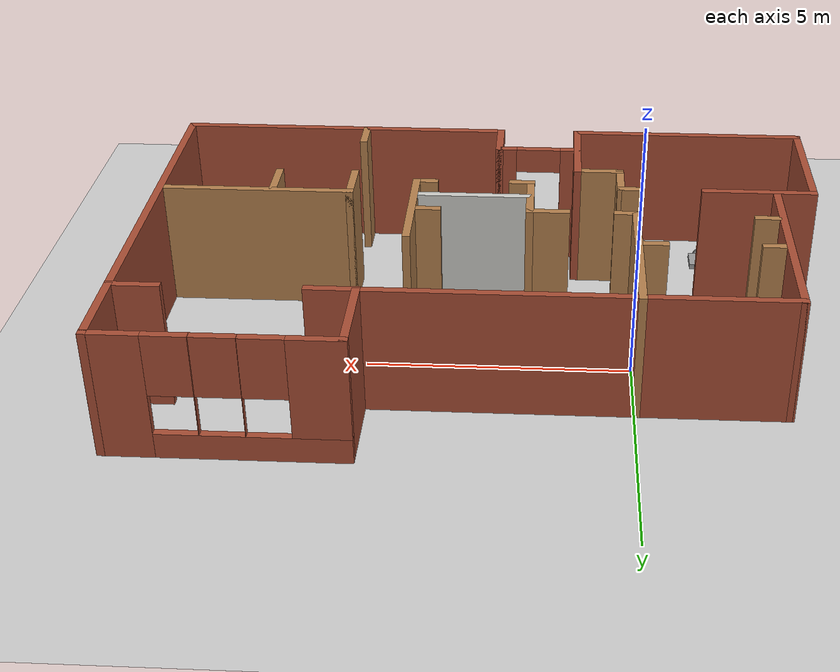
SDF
<sdf version="1.7">
 <world name="default">
  <plugin name="welcome" filename="libwelcome.so"/>
  <light name="sun" type="directional">
   <pose>0 0 10 0 -0 0</pose>
   <diffuse>0.8 0.8 0.8 1</diffuse>
   <specular>0.2 0.2 0.2 1</specular>
   <attenuation>
    <range>1000</range>
    <constant>0.9</constant>
    <linear>0.01</linear>
    <quadratic>0.001</quadratic>
   </attenuation>
   <direction>-0.5 0.1 -0.9</direction>
   <spot><inner_angle>0</inner_angle><outer_angle>0</outer_angle><falloff>0</falloff></spot>
  </light>
  <model name="ground_plane">
   <static>1</static>
   <link name="link">
    <collision name="collision">
     <geometry><plane><normal>0 0 1</normal><size>100 100</size></plane></geometry>
     <surface>
      <contact><collide_bitmask>65535</collide_bitmask></contact>
      <friction><ode><mu>100</mu><mu2>50</mu2></ode></friction>
     </surface>
    </collision>
    <visual name="visual">
     <cast_shadows>0</cast_shadows>
     <geometry><plane><normal>0 0 1</normal><size>100 100</size></plane></geometry>
     <material>
      <script><uri>file://media/materials/scripts/gazebo.material</uri><name>Gazebo/Grey</name></script>
     </material>
    </visual>
   </link>
  </model>
  <gravity>0 0 -9.8</gravity>
  <magnetic_field>6e-06 2.3e-05 -4.2e-05</magnetic_field>
  <atmosphere type="adiabatic"/>
  <physics name="default_physics" default="0" type="ode">
   <max_step_size>0.001</max_step_size>
   <real_time_factor>1</real_time_factor>
   <real_time_update_rate>1000</real_time_update_rate>
  </physics>
  <scene><ambient>0.4 0.4 0.4 1</ambient><background>0.7 0.7 0.7 1</background><shadows>1</shadows></scene>
  <spherical_coordinates>
   <surface_model>EARTH_WGS84</surface_model>
   <latitude_deg>0</latitude_deg>
   <longitude_deg>0</longitude_deg>
   <elevation>0</elevation>
   <heading_deg>0</heading_deg>
  </spherical_coordinates>
  <model name="building">
   <pose>2.885 -1.15 0 0 -0 0</pose>
   <link name="Wall_0">
    <collision name="Wall_0_Collision">
     <geometry><box><size>2.25 0.15 2.5</size></box></geometry>
     <pose>0 0 1.25 0 -0 0</pose>
    </collision>
    <visual name="Wall_0_Visual">
     <pose>0 0 1.25 0 -0 0</pose>
     <geometry><box><size>2.25 0.15 2.5</size></box></geometry>
     <material>
      <script><uri>file://media/materials/scripts/gazebo.material</uri><name>Gazebo/Bricks</name></script>
      <ambient>1 1 1 1</ambient>
     </material>
     <meta><layer>0</layer></meta>
    </visual>
    <pose>-5.355 -1.58 0 0 -0 3.14159</pose>
   </link>
   <link name="Wall_1">
    <collision name="Wall_1_Collision">
     <geometry><box><size>2.75 0.15 2.5</size></box></geometry>
     <pose>0 0 1.25 0 -0 0</pose>
    </collision>
    <visual name="Wall_1_Visual">
     <pose>0 0 1.25 0 -0 0</pose>
     <geometry><box><size>2.75 0.15 2.5</size></box></geometry>
     <material>
      <script><uri>file://media/materials/scripts/gazebo.material</uri><name>Gazebo/Bricks</name></script>
      <ambient>1 1 1 1</ambient>
     </material>
     <meta><layer>0</layer></meta>
    </visual>
    <pose>-6.405 -2.88 0 0 0 -1.5708</pose>
   </link>
   <link name="Wall_11">
    <collision name="Wall_11_Collision">
     <geometry><box><size>0.5 0.15 2.5</size></box></geometry>
     <pose>0 0 1.25 0 -0 0</pose>
    </collision>
    <visual name="Wall_11_Visual">
     <pose>0 0 1.25 0 -0 0</pose>
     <geometry><box><size>0.5 0.15 2.5</size></box></geometry>
     <material>
      <script><uri>file://media/materials/scripts/gazebo.material</uri><name>Gazebo/Wood</name></script>
      <ambient>1 1 1 1</ambient>
     </material>
     <meta><layer>0</layer></meta>
    </visual>
    <pose>-5.42054 0.610454 0 0 -0 0</pose>
   </link>
   <link name="Wall_13">
    <collision name="Wall_13_Collision">
     <geometry><box><size>3.25 0.15 2.5</size></box></geometry>
     <pose>0 0 1.25 0 -0 0</pose>
    </collision>
    <visual name="Wall_13_Visual">
     <pose>0 0 1.25 0 -0 0</pose>
     <geometry><box><size>3.25 0.15 2.5</size></box></geometry>
     <material>
      <script><uri>file://media/materials/scripts/gazebo.material</uri><name>Gazebo/Wood</name></script>
      <ambient>1 1 1 1</ambient>
     </material>
     <meta><layer>0</layer></meta>
    </visual>
    <pose>-2.915 1 0 0 0 -1.5708</pose>
   </link>
   <link name="Wall_14">
    <collision name="Wall_14_Collision">
     <geometry><box><size>0.5 0.15 2.5</size></box></geometry>
     <pose>0 0 1.25 0 -0 0</pose>
    </collision>
    <visual name="Wall_14_Visual">
     <pose>0 0 1.25 0 -0 0</pose>
     <geometry><box><size>0.5 0.15 2.5</size></box></geometry>
     <material>
      <script><uri>file://media/materials/scripts/gazebo.material</uri><name>Gazebo/Wood</name></script>
      <ambient>1 1 1 1</ambient>
     </material>
     <meta><layer>0</layer></meta>
    </visual>
    <pose>-2.74 -0.55 0 0 -0 0</pose>
   </link>
   <link name="Wall_16">
    <collision name="Wall_16_Collision">
     <geometry><box><size>0.5 0.15 2.5</size></box></geometry>
     <pose>0 0 1.25 0 -0 0</pose>
    </collision>
    <visual name="Wall_16_Visual">
     <pose>0 0 1.25 0 -0 0</pose>
     <geometry><box><size>0.5 0.15 2.5</size></box></geometry>
     <material>
      <script><uri>file://media/materials/scripts/gazebo.material</uri><name>Gazebo/Wood</name></script>
      <ambient>1 1 1 1</ambient>
     </material>
     <meta><layer>0</layer></meta>
    </visual>
    <pose>-5.39507 -0.487783 0 0 -0 0</pose>
   </link>
   <link name="Wall_18">
    <collision name="Wall_18_Collision">
     <geometry><box><size>0.5 0.15 2.5</size></box></geometry>
     <pose>0 0 1.25 0 -0 0</pose>
    </collision>
    <visual name="Wall_18_Visual">
     <pose>0 0 1.25 0 -0 0</pose>
     <geometry><box><size>0.5 0.15 2.5</size></box></geometry>
     <material>
      <script><uri>file://media/materials/scripts/gazebo.material</uri><name>Gazebo/Wood</name></script>
      <ambient>1 1 1 1</ambient>
     </material>
     <meta><layer>0</layer></meta>
    </visual>
    <pose>-3.22609 0.62703 0 0 -0 3.14159</pose>
   </link>
   <link name="Wall_2">
    <collision name="Wall_2_Collision">
     <geometry><box><size>4.75 0.15 2.5</size></box></geometry>
     <pose>0 0 1.25 0 -0 0</pose>
    </collision>
    <visual name="Wall_2_Visual">
     <pose>0 0 1.25 0 -0 0</pose>
     <geometry><box><size>4.75 0.15 2.5</size></box></geometry>
     <material>
      <script><uri>file://media/materials/scripts/gazebo.material</uri><name>Gazebo/Bricks</name></script>
      <ambient>1 1 1 1</ambient>
     </material>
     <meta><layer>0</layer></meta>
    </visual>
    <pose>-4.105 -4.18 0 0 -0 0</pose>
   </link>
   <link name="Wall_20">
    <pose>-0.995 -3.32 0 0 -0 0</pose>
    <visual name="Wall_20_Visual_0">
     <pose>-0.666369 0 1.25 0 -0 0</pose>
     <geometry><box><size>0.417262 0.15 2.5</size></box></geometry>
     <material>
      <script><uri>file://media/materials/scripts/gazebo.material</uri><name>Gazebo/Bricks</name></script>
      <ambient>1 1 1 1</ambient>
     </material>
     <meta><layer>0</layer></meta>
    </visual>
    <collision name="Wall_20_Collision_0">
     <geometry><box><size>0.417262 0.15 2.5</size></box></geometry>
     <pose>-0.666369 0 1.25 0 -0 0</pose>
    </collision>
    <visual name="Wall_20_Visual_1">
     <pose>0.658631 0 1.25 0 -0 0</pose>
     <geometry><box><size>0.432738 0.15 2.5</size></box></geometry>
     <material>
      <script><uri>file://media/materials/scripts/gazebo.material</uri><name>Gazebo/Bricks</name></script>
      <ambient>1 1 1 1</ambient>
     </material>
     <meta><layer>0</layer></meta>
    </visual>
    <collision name="Wall_20_Collision_1">
     <geometry><box><size>0.432738 0.15 2.5</size></box></geometry>
     <pose>0.658631 0 1.25 0 -0 0</pose>
    </collision>
    <visual name="Wall_20_Visual_2">
     <pose>-0.007738 0 2.25 0 -0 0</pose>
     <geometry><box><size>0.9 0.15 0.5</size></box></geometry>
     <material>
      <script><uri>file://media/materials/scripts/gazebo.material</uri><name>Gazebo/Bricks</name></script>
      <ambient>1 1 1 1</ambient>
     </material>
     <meta><layer>0</layer></meta>
    </visual>
    <collision name="Wall_20_Collision_2">
     <geometry><box><size>0.9 0.15 0.5</size></box></geometry>
     <pose>-0.007738 0 2.25 0 -0 0</pose>
    </collision>
   </link>
   <link name="Wall_21">
    <collision name="Wall_21_Collision">
     <geometry><box><size>1 0.15 2.5</size></box></geometry>
     <pose>0 0 1.25 0 -0 0</pose>
    </collision>
    <visual name="Wall_21_Visual">
     <pose>0 0 1.25 0 -0 0</pose>
     <geometry><box><size>1 0.15 2.5</size></box></geometry>
     <material>
      <script><uri>file://media/materials/scripts/gazebo.material</uri><name>Gazebo/Bricks</name></script>
      <ambient>1 1 1 1</ambient>
     </material>
     <meta><layer>0</layer></meta>
    </visual>
    <pose>-0.195 -3.745 0 0 0 -1.5708</pose>
   </link>
   <link name="Wall_22">
    <collision name="Wall_22_Collision">
     <geometry><box><size>6.75 0.15 2.5</size></box></geometry>
     <pose>0 0 1.25 0 -0 0</pose>
    </collision>
    <visual name="Wall_22_Visual">
     <pose>0 0 1.25 0 -0 0</pose>
     <geometry><box><size>6.75 0.15 2.5</size></box></geometry>
     <material>
      <script><uri>file://media/materials/scripts/gazebo.material</uri><name>Gazebo/Bricks</name></script>
      <ambient>1 1 1 1</ambient>
     </material>
     <meta><layer>0</layer></meta>
    </visual>
    <pose>3.105 -4.17 0 0 -0 0</pose>
   </link>
   <link name="Wall_23">
    <collision name="Wall_23_Collision">
     <geometry><box><size>8.5 0.15 2.5</size></box></geometry>
     <pose>0 0 1.25 0 -0 0</pose>
    </collision>
    <visual name="Wall_23_Visual">
     <pose>0 0 1.25 0 -0 0</pose>
     <geometry><box><size>8.5 0.15 2.5</size></box></geometry>
     <material>
      <script><uri>file://media/materials/scripts/gazebo.material</uri><name>Gazebo/Bricks</name></script>
      <ambient>1 1 1 1</ambient>
     </material>
     <meta><layer>0</layer></meta>
    </visual>
    <pose>6.405 0.005 0 0 -0 1.5708</pose>
   </link>
   <link name="Wall_25">
    <pose>4.23 4.18 0 0 -0 3.14159</pose>
    <visual name="Wall_25_Visual_0">
     <pose>-1.7302 0 1.25 0 -0 0</pose>
     <geometry><box><size>1.0396 0.15 2.5</size></box></geometry>
     <material>
      <script><uri>file://media/materials/scripts/gazebo.material</uri><name>Gazebo/Bricks</name></script>
      <ambient>1 1 1 1</ambient>
     </material>
     <meta><layer>0</layer></meta>
    </visual>
    <collision name="Wall_25_Collision_0">
     <geometry><box><size>1.0396 0.15 2.5</size></box></geometry>
     <pose>-1.7302 0 1.25 0 -0 0</pose>
    </collision>
    <visual name="Wall_25_Visual_1">
     <pose>0.519799 0 0.25 0 -0 0</pose>
     <geometry><box><size>3.4604 0.15 0.5</size></box></geometry>
     <material>
      <script><uri>file://media/materials/scripts/gazebo.material</uri><name>Gazebo/Bricks</name></script>
      <ambient>1 1 1 1</ambient>
     </material>
     <meta><layer>0</layer></meta>
    </visual>
    <collision name="Wall_25_Collision_1">
     <geometry><box><size>3.4604 0.15 0.5</size></box></geometry>
     <pose>0.519799 0 0.25 0 -0 0</pose>
    </collision>
    <visual name="Wall_25_Visual_2">
     <pose>-0.403907 0 1.5 0 -0 0</pose>
     <geometry><box><size>0.01299 0.15 2</size></box></geometry>
     <material>
      <script><uri>file://media/materials/scripts/gazebo.material</uri><name>Gazebo/Bricks</name></script>
      <ambient>1 1 1 1</ambient>
     </material>
     <meta><layer>0</layer></meta>
    </visual>
    <collision name="Wall_25_Collision_2">
     <geometry><box><size>0.01299 0.15 2</size></box></geometry>
     <pose>-0.403907 0 1.5 0 -0 0</pose>
    </collision>
    <visual name="Wall_25_Visual_3">
     <pose>0.406241 0 1.5 0 -0 0</pose>
     <geometry><box><size>0.007305 0.15 2</size></box></geometry>
     <material>
      <script><uri>file://media/materials/scripts/gazebo.material</uri><name>Gazebo/Bricks</name></script>
      <ambient>1 1 1 1</ambient>
     </material>
     <meta><layer>0</layer></meta>
    </visual>
    <collision name="Wall_25_Collision_3">
     <geometry><box><size>0.007305 0.15 2</size></box></geometry>
     <pose>0.406241 0 1.5 0 -0 0</pose>
    </collision>
    <visual name="Wall_25_Visual_4">
     <pose>1.72995 0 1.5 0 -0 0</pose>
     <geometry><box><size>1.04011 0.15 2</size></box></geometry>
     <material>
      <script><uri>file://media/materials/scripts/gazebo.material</uri><name>Gazebo/Bricks</name></script>
      <ambient>1 1 1 1</ambient>
     </material>
     <meta><layer>0</layer></meta>
    </visual>
    <collision name="Wall_25_Collision_4">
     <geometry><box><size>1.04011 0.15 2</size></box></geometry>
     <pose>1.72995 0 1.5 0 -0 0</pose>
    </collision>
    <visual name="Wall_25_Visual_5">
     <pose>-0.810402 0 1.9 0 -0 0</pose>
     <geometry><box><size>0.8 0.15 1.2</size></box></geometry>
     <material>
      <script><uri>file://media/materials/scripts/gazebo.material</uri><name>Gazebo/Bricks</name></script>
      <ambient>1 1 1 1</ambient>
     </material>
     <meta><layer>0</layer></meta>
    </visual>
    <collision name="Wall_25_Collision_5">
     <geometry><box><size>0.8 0.15 1.2</size></box></geometry>
     <pose>-0.810402 0 1.9 0 -0 0</pose>
    </collision>
    <visual name="Wall_25_Visual_6">
     <pose>0.002588 0 1.9 0 -0 0</pose>
     <geometry><box><size>0.8 0.15 1.2</size></box></geometry>
     <material>
      <script><uri>file://media/materials/scripts/gazebo.material</uri><name>Gazebo/Bricks</name></script>
      <ambient>1 1 1 1</ambient>
     </material>
     <meta><layer>0</layer></meta>
    </visual>
    <collision name="Wall_25_Collision_6">
     <geometry><box><size>0.8 0.15 1.2</size></box></geometry>
     <pose>0.002588 0 1.9 0 -0 0</pose>
    </collision>
    <visual name="Wall_25_Visual_7">
     <pose>0.809894 0 1.9 0 -0 0</pose>
     <geometry><box><size>0.8 0.15 1.2</size></box></geometry>
     <material>
      <script><uri>file://media/materials/scripts/gazebo.material</uri><name>Gazebo/Bricks</name></script>
      <ambient>1 1 1 1</ambient>
     </material>
     <meta><layer>0</layer></meta>
    </visual>
    <collision name="Wall_25_Collision_7">
     <geometry><box><size>0.8 0.15 1.2</size></box></geometry>
     <pose>0.809894 0 1.9 0 -0 0</pose>
    </collision>
   </link>
   <link name="Wall_26">
    <collision name="Wall_26_Collision">
     <geometry><box><size>1.75 0.15 2.5</size></box></geometry>
     <pose>0 0 1.25 0 -0 0</pose>
    </collision>
    <visual name="Wall_26_Visual">
     <pose>0 0 1.25 0 -0 0</pose>
     <geometry><box><size>1.75 0.15 2.5</size></box></geometry>
     <material>
      <script><uri>file://media/materials/scripts/gazebo.material</uri><name>Gazebo/Bricks</name></script>
      <ambient>1 1 1 1</ambient>
     </material>
     <meta><layer>0</layer></meta>
    </visual>
    <pose>2.055 3.38 0 0 0 -1.5708</pose>
   </link>
   <link name="Wall_28">
    <collision name="Wall_28_Collision">
     <geometry><box><size>1 0.15 2.5</size></box></geometry>
     <pose>0 0 1.25 0 -0 0</pose>
    </collision>
    <visual name="Wall_28_Visual">
     <pose>0 0 1.25 0 -0 0</pose>
     <geometry><box><size>1 0.15 2.5</size></box></geometry>
     <material>
      <script><uri>file://media/materials/scripts/gazebo.material</uri><name>Gazebo/Bricks</name></script>
      <ambient>1 1 1 1</ambient>
     </material>
     <meta><layer>0</layer></meta>
    </visual>
    <pose>5.98 2.58 0 0 -0 3.14159</pose>
   </link>
   <link name="Wall_3">
    <collision name="Wall_3_Collision">
     <geometry><box><size>1.98 0.15 2.5</size></box></geometry>
     <pose>0 0 1.25 0 -0 0</pose>
    </collision>
    <visual name="Wall_3_Visual">
     <pose>0 0 1.25 0 -0 0</pose>
     <geometry><box><size>1.98 0.15 2.5</size></box></geometry>
     <material>
      <script><uri>file://media/materials/scripts/gazebo.material</uri><name>Gazebo/Bricks</name></script>
      <ambient>1 1 1 1</ambient>
     </material>
     <meta><layer>0</layer></meta>
    </visual>
    <pose>-1.805 -3.265 0 0 -0 1.5708</pose>
   </link>
   <link name="Wall_30">
    <collision name="Wall_30_Collision">
     <geometry><box><size>0.75 0.15 2.5</size></box></geometry>
     <pose>0 0 1.25 0 -0 0</pose>
    </collision>
    <visual name="Wall_30_Visual">
     <pose>0 0 1.25 0 -0 0</pose>
     <geometry><box><size>0.75 0.15 2.5</size></box></geometry>
     <material>
      <script><uri>file://media/materials/scripts/gazebo.material</uri><name>Gazebo/Wood</name></script>
      <ambient>1 1 1 1</ambient>
     </material>
     <meta><layer>0</layer></meta>
    </visual>
    <pose>2.655 -3.85 0 0 -0 1.5708</pose>
   </link>
   <link name="Wall_32">
    <collision name="Wall_32_Collision">
     <geometry><box><size>1 0.15 2.5</size></box></geometry>
     <pose>0 0 1.25 0 -0 0</pose>
    </collision>
    <visual name="Wall_32_Visual">
     <pose>0 0 1.25 0 -0 0</pose>
     <geometry><box><size>1 0.15 2.5</size></box></geometry>
     <material>
      <script><uri>file://media/materials/scripts/gazebo.material</uri><name>Gazebo/Wood</name></script>
      <ambient>1 1 1 1</ambient>
     </material>
     <meta><layer>0</layer></meta>
    </visual>
    <pose>2.655 -1.635 0 0 -0 1.5708</pose>
   </link>
   <link name="Wall_33">
    <collision name="Wall_33_Collision">
     <geometry><box><size>3.75 0.15 2.5</size></box></geometry>
     <pose>0 0 1.25 0 -0 0</pose>
    </collision>
    <visual name="Wall_33_Visual">
     <pose>0 0 1.25 0 -0 0</pose>
     <geometry><box><size>3.75 0.15 2.5</size></box></geometry>
     <material>
      <script><uri>file://media/materials/scripts/gazebo.material</uri><name>Gazebo/Wood</name></script>
      <ambient>1 1 1 1</ambient>
     </material>
     <meta><layer>0</layer></meta>
    </visual>
    <pose>4.455 -1.21 0 0 -0 0</pose>
   </link>
   <link name="Wall_35">
    <collision name="Wall_35_Collision">
     <geometry><box><size>0.9 0.15 2.5</size></box></geometry>
     <pose>0 0 1.25 0 -0 0</pose>
    </collision>
    <visual name="Wall_35_Visual">
     <pose>0 0 1.25 0 -0 0</pose>
     <geometry><box><size>0.9 0.15 2.5</size></box></geometry>
     <material>
      <script><uri>file://media/materials/scripts/gazebo.material</uri><name>Gazebo/Wood</name></script>
      <ambient>1 1 1 1</ambient>
     </material>
     <meta><layer>0</layer></meta>
    </visual>
    <pose>4.17527 -1.65644 0 0 0 -1.5708</pose>
   </link>
   <link name="Wall_37">
    <collision name="Wall_37_Collision">
     <geometry><box><size>0.846 0.15 2.5</size></box></geometry>
     <pose>0 0 1.25 0 -0 0</pose>
    </collision>
    <visual name="Wall_37_Visual">
     <pose>0 0 1.25 0 -0 0</pose>
     <geometry><box><size>0.846 0.15 2.5</size></box></geometry>
     <material>
      <script><uri>file://media/materials/scripts/gazebo.material</uri><name>Gazebo/Wood</name></script>
      <ambient>1 1 1 1</ambient>
     </material>
     <meta><layer>0</layer></meta>
    </visual>
    <pose>-1.233 -0.55 0 0 -0 0</pose>
   </link>
   <link name="Wall_38">
    <collision name="Wall_38_Collision">
     <geometry><box><size>1.36702 0.15 2.5</size></box></geometry>
     <pose>0 0 1.25 0 -0 0</pose>
    </collision>
    <visual name="Wall_38_Visual">
     <pose>0 0 1.25 0 -0 0</pose>
     <geometry><box><size>1.36702 0.15 2.5</size></box></geometry>
     <material>
      <script><uri>file://media/materials/scripts/gazebo.material</uri><name>Gazebo/Wood</name></script>
      <ambient>1 1 1 1</ambient>
     </material>
     <meta><layer>0</layer></meta>
    </visual>
    <pose>-0.885 -1.1585 0 0 0 -1.5708</pose>
   </link>
   <link name="Wall_39">
    <collision name="Wall_39_Collision">
     <geometry><box><size>0.509293 0.15 2.5</size></box></geometry>
     <pose>0 0 1.25 0 -0 0</pose>
    </collision>
    <visual name="Wall_39_Visual">
     <pose>0 0 1.25 0 -0 0</pose>
     <geometry><box><size>0.509293 0.15 2.5</size></box></geometry>
     <material>
      <script><uri>file://media/materials/scripts/gazebo.material</uri><name>Gazebo/Wood</name></script>
      <ambient>1 1 1 1</ambient>
     </material>
     <meta><layer>0</layer></meta>
    </visual>
    <pose>-0.705354 -1.7669 0 0 -0 0.000544</pose>
   </link>
   <link name="Wall_4">
    <collision name="Wall_4_Collision">
     <geometry><box><size>1 0.15 2.5</size></box></geometry>
     <pose>0 0 1.25 0 -0 0</pose>
    </collision>
    <visual name="Wall_4_Visual">
     <pose>0 0 1.25 0 -0 0</pose>
     <geometry><box><size>1 0.15 2.5</size></box></geometry>
     <material>
      <script><uri>file://media/materials/scripts/gazebo.material</uri><name>Gazebo/Wood</name></script>
      <ambient>1 1 1 1</ambient>
     </material>
     <meta><layer>0</layer></meta>
    </visual>
    <pose>-2.23 -2.35 0 0 -0 3.14159</pose>
   </link>
   <link name="Wall_41">
    <collision name="Wall_41_Collision">
     <geometry><box><size>0.5 0.15 2.5</size></box></geometry>
     <pose>0 0 1.25 0 -0 0</pose>
    </collision>
    <visual name="Wall_41_Visual">
     <pose>0 0 1.25 0 -0 0</pose>
     <geometry><box><size>0.5 0.15 2.5</size></box></geometry>
     <material>
      <script><uri>file://media/materials/scripts/gazebo.material</uri><name>Gazebo/Wood</name></script>
      <ambient>1 1 1 1</ambient>
     </material>
     <meta><layer>0</layer></meta>
    </visual>
    <pose>1.20247 -1.73362 0 0 -0 0</pose>
   </link>
   <link name="Wall_42">
    <collision name="Wall_42_Collision">
     <geometry><box><size>2.40993 0.15 2.5</size></box></geometry>
     <pose>0 0 1.25 0 -0 0</pose>
    </collision>
    <visual name="Wall_42_Visual">
     <pose>0 0 1.25 0 -0 0</pose>
     <geometry><box><size>2.40993 0.15 2.5</size></box></geometry>
     <material>
      <script><uri>file://media/materials/scripts/gazebo.material</uri><name>Gazebo/Wood</name></script>
      <ambient>1 1 1 1</ambient>
     </material>
     <meta><layer>0</layer></meta>
    </visual>
    <pose>1.38031 -0.603662 0 0 -0 1.57331</pose>
   </link>
   <link name="Wall_44">
    <collision name="Wall_44_Collision">
     <geometry><box><size>2.25 0.15 2.5</size></box></geometry>
     <pose>0 0 1.25 0 -0 0</pose>
    </collision>
    <visual name="Wall_44_Visual">
     <pose>0 0 1.25 0 -0 0</pose>
     <geometry><box><size>2.25 0.15 2.5</size></box></geometry>
     <material>
      <script><uri>file://media/materials/scripts/gazebo.material</uri><name>Gazebo/CeilingTiled</name></script>
      <ambient>1 1 1 1</ambient>
     </material>
     <meta><layer>0</layer></meta>
    </visual>
    <pose>0.223792 -1.16 0 0 -0 0</pose>
   </link>
   <link name="Wall_46">
    <collision name="Wall_46_Collision">
     <geometry><box><size>0.5 0.15 2.5</size></box></geometry>
     <pose>0 0 1.25 0 -0 0</pose>
    </collision>
    <visual name="Wall_46_Visual">
     <pose>0 0 1.25 0 -0 0</pose>
     <geometry><box><size>0.5 0.15 2.5</size></box></geometry>
     <material>
      <script><uri>file://media/materials/scripts/gazebo.material</uri><name>Gazebo/Wood</name></script>
      <ambient>1 1 1 1</ambient>
     </material>
     <meta><layer>0</layer></meta>
    </visual>
    <pose>1.06568 -0.560964 0 0 -0 3.14159</pose>
   </link>
   <link name="Wall_5">
    <collision name="Wall_5_Collision">
     <geometry><box><size>0.92 0.15 2.5</size></box></geometry>
     <pose>0 0 1.25 0 -0 0</pose>
    </collision>
    <visual name="Wall_5_Visual">
     <pose>0 0 1.25 0 -0 0</pose>
     <geometry><box><size>0.92 0.15 2.5</size></box></geometry>
     <material>
      <script><uri>file://media/materials/scripts/gazebo.material</uri><name>Gazebo/Wood</name></script>
      <ambient>1 1 1 1</ambient>
     </material>
     <meta><layer>0</layer></meta>
    </visual>
    <pose>-2.655 -1.965 0 0 -0 1.5708</pose>
   </link>
   <link name="Wall_6">
    <collision name="Wall_6_Collision">
     <geometry><box><size>0.493495 0.15 2.5</size></box></geometry>
     <pose>0 0 1.25 0 -0 0</pose>
    </collision>
    <visual name="Wall_6_Visual">
     <pose>0 0 1.25 0 -0 0</pose>
     <geometry><box><size>0.493495 0.15 2.5</size></box></geometry>
     <material>
      <script><uri>file://media/materials/scripts/gazebo.material</uri><name>Gazebo/Wood</name></script>
      <ambient>1 1 1 1</ambient>
     </material>
     <meta><layer>0</layer></meta>
    </visual>
    <pose>-2.8265 -1.58 0 0 -0 3.14159</pose>
   </link>
   <link name="Wall_8">
    <collision name="Wall_8_Collision">
     <geometry><box><size>4.25 0.15 2.5</size></box></geometry>
     <pose>0 0 1.25 0 -0 0</pose>
    </collision>
    <visual name="Wall_8_Visual">
     <pose>0 0 1.25 0 -0 0</pose>
     <geometry><box><size>4.25 0.15 2.5</size></box></geometry>
     <material>
      <script><uri>file://media/materials/scripts/gazebo.material</uri><name>Gazebo/Bricks</name></script>
      <ambient>1 1 1 1</ambient>
     </material>
     <meta><layer>0</layer></meta>
    </visual>
    <pose>-5.685 0.5 0 0 -0 1.5708</pose>
   </link>
   <link name="Wall_9">
    <collision name="Wall_9_Collision">
     <geometry><box><size>8.75 0.15 2.5</size></box></geometry>
     <pose>0 0 1.25 0 -0 0</pose>
    </collision>
    <visual name="Wall_9_Visual">
     <pose>0 0 1.25 0 -0 0</pose>
     <geometry><box><size>8.75 0.15 2.5</size></box></geometry>
     <material>
      <script><uri>file://media/materials/scripts/gazebo.material</uri><name>Gazebo/Bricks</name></script>
      <ambient>1 1 1 1</ambient>
     </material>
     <meta><layer>0</layer></meta>
    </visual>
    <pose>-1.385 2.55 0 0 -0 0</pose>
   </link>
   <static>1</static>
  </model>
  <model name="cart">
   <link name="link_0_clone">
    <pose>-0.250001 -0 0 0 -0 0</pose>
    <inertial>
     <mass>1</mass>
     <inertia>
      <ixx>0.166667</ixx>
      <ixy>0</ixy>
      <ixz>0</ixz>
      <iyy>0.166667</iyy>
      <iyz>0</iyz>
      <izz>0.166667</izz>
     </inertia>
    </inertial>
    <visual name="visual">
     <geometry><box><size>0.5 0.5 0.1</size></box></geometry>
     <material>
      <lighting>1</lighting>
      <script><uri>file://media/materials/scripts/gazebo.material</uri><name>Gazebo/Grey</name></script>
      <shader type="pixel"><normal_map>__default__</normal_map></shader>
      <ambient>0.3 0.3 0.3 1</ambient>
      <diffuse>0.7 0.7 0.7 1</diffuse>
      <specular>0.01 0.01 0.01 1</specular>
      <emissive>0 0 0 1</emissive>
     </material>
    </visual>
    <collision name="collision">
     <geometry><box><size>0.5 0.5 0.1</size></box></geometry>
     <surface>
      <friction>
       <ode><mu>1</mu><mu2>1</mu2><fdir1>0 0 0</fdir1><slip1>0</slip1><slip2>0</slip2></ode>
       <torsional>
        <coefficient>1</coefficient>
        <patch_radius>0</patch_radius>
        <surface_radius>0</surface_radius>
        <use_patch_radius>1</use_patch_radius>
        <ode><slip>0</slip></ode>
       </torsional>
      </friction>
      <bounce><restitution_coefficient>0</restitution_coefficient><threshold>1e+06</threshold></bounce>
      <contact>
       <collide_without_contact>0</collide_without_contact>
       <collide_without_contact_bitmask>1</collide_without_contact_bitmask>
       <collide_bitmask>1</collide_bitmask>
       <ode>
        <soft_cfm>0</soft_cfm>
        <soft_erp>0.2</soft_erp>
        <kp>1e+13</kp>
        <kd>1</kd>
        <max_vel>0.01</max_vel>
        <min_depth>0</min_depth>
       </ode>
       <bullet>
        <split_impulse>1</split_impulse>
        <split_impulse_penetration_threshold>-0.01</split_impulse_penetration_threshold>
        <soft_cfm>0</soft_cfm>
        <soft_erp>0.2</soft_erp>
        <kp>1e+13</kp>
        <kd>1</kd>
       </bullet>
      </contact>
     </surface>
    </collision>
   </link>
   <link name="link_0_clone_0">
    <pose>0.249999 -0 0 0 -0 0</pose>
    <inertial>
     <mass>1</mass>
     <inertia>
      <ixx>0.166667</ixx>
      <ixy>0</ixy>
      <ixz>0</ixz>
      <iyy>0.166667</iyy>
      <iyz>0</iyz>
      <izz>0.166667</izz>
     </inertia>
    </inertial>
    <visual name="visual">
     <geometry><box><size>0.5 0.5 0.1</size></box></geometry>
     <material>
      <lighting>1</lighting>
      <script><uri>file://media/materials/scripts/gazebo.material</uri><name>Gazebo/Grey</name></script>
      <shader type="pixel"><normal_map>__default__</normal_map></shader>
      <ambient>0.3 0.3 0.3 1</ambient>
      <diffuse>0.7 0.7 0.7 1</diffuse>
      <specular>0.01 0.01 0.01 1</specular>
      <emissive>0 0 0 1</emissive>
     </material>
    </visual>
    <collision name="collision">
     <geometry><box><size>0.5 0.5 0.1</size></box></geometry>
     <surface>
      <friction>
       <ode><mu>1</mu><mu2>1</mu2><fdir1>0 0 0</fdir1><slip1>0</slip1><slip2>0</slip2></ode>
       <torsional>
        <coefficient>1</coefficient>
        <patch_radius>0</patch_radius>
        <surface_radius>0</surface_radius>
        <use_patch_radius>1</use_patch_radius>
        <ode><slip>0</slip></ode>
       </torsional>
      </friction>
      <bounce><restitution_coefficient>0</restitution_coefficient><threshold>1e+06</threshold></bounce>
      <contact>
       <collide_without_contact>0</collide_without_contact>
       <collide_without_contact_bitmask>1</collide_without_contact_bitmask>
       <collide_bitmask>1</collide_bitmask>
       <ode>
        <soft_cfm>0</soft_cfm>
        <soft_erp>0.2</soft_erp>
        <kp>1e+13</kp>
        <kd>1</kd>
        <max_vel>0.01</max_vel>
        <min_depth>0</min_depth>
       </ode>
       <bullet>
        <split_impulse>1</split_impulse>
        <split_impulse_penetration_threshold>-0.01</split_impulse_penetration_threshold>
        <soft_cfm>0</soft_cfm>
        <soft_erp>0.2</soft_erp>
        <kp>1e+13</kp>
        <kd>1</kd>
       </bullet>
      </contact>
     </surface>
    </collision>
   </link>
   <link name="link_1_clone">
    <pose>-0.250001 -0.275119 0 0 -0 0</pose>
    <inertial>
     <mass>1</mass>
     <inertia><ixx>0.145833</ixx><ixy>0</ixy><ixz>0</ixz><iyy>0.145833</iyy><iyz>0</iyz><izz>0.125</izz></inertia>
    </inertial>
    <visual name="visual">
     <pose>0 0 0 1.57 -0 0</pose>
     <geometry><cylinder><radius>0.15</radius><length>0.05</length></cylinder></geometry>
     <material>
      <lighting>1</lighting>
      <script><uri>file://media/materials/scripts/gazebo.material</uri><name>Gazebo/Grey</name></script>
      <shader type="pixel"><normal_map>__default__</normal_map></shader>
      <ambient>0.3 0.3 0.3 1</ambient>
      <diffuse>0.7 0.7 0.7 1</diffuse>
      <specular>0.01 0.01 0.01 1</specular>
      <emissive>0 0 0 1</emissive>
     </material>
    </visual>
    <collision name="collision">
     <pose>0 0 0 1.5707 -0 0</pose>
     <geometry><cylinder><radius>0.15</radius><length>0.05</length></cylinder></geometry>
     <surface>
      <friction>
       <ode><mu>1</mu><mu2>1</mu2><fdir1>0 0 0</fdir1><slip1>0</slip1><slip2>0</slip2></ode>
       <torsional>
        <coefficient>1</coefficient>
        <patch_radius>0</patch_radius>
        <surface_radius>0</surface_radius>
        <use_patch_radius>1</use_patch_radius>
        <ode><slip>0</slip></ode>
       </torsional>
      </friction>
      <bounce><restitution_coefficient>0</restitution_coefficient><threshold>1e+06</threshold></bounce>
      <contact>
       <collide_without_contact>0</collide_without_contact>
       <collide_without_contact_bitmask>1</collide_without_contact_bitmask>
       <collide_bitmask>1</collide_bitmask>
       <ode>
        <soft_cfm>0</soft_cfm>
        <soft_erp>0.2</soft_erp>
        <kp>1e+13</kp>
        <kd>1</kd>
        <max_vel>0.01</max_vel>
        <min_depth>0</min_depth>
       </ode>
       <bullet>
        <split_impulse>1</split_impulse>
        <split_impulse_penetration_threshold>-0.01</split_impulse_penetration_threshold>
        <soft_cfm>0</soft_cfm>
        <soft_erp>0.2</soft_erp>
        <kp>1e+13</kp>
        <kd>1</kd>
       </bullet>
      </contact>
     </surface>
    </collision>
   </link>
   <link name="link_1_clone_0">
    <pose>-0.250001 0.275119 0 0 -0 0</pose>
    <inertial>
     <mass>1</mass>
     <inertia><ixx>0.145833</ixx><ixy>0</ixy><ixz>0</ixz><iyy>0.145833</iyy><iyz>0</iyz><izz>0.125</izz></inertia>
    </inertial>
    <visual name="visual">
     <pose>0 0 0 1.57 -0 0</pose>
     <geometry><cylinder><radius>0.15</radius><length>0.05</length></cylinder></geometry>
     <material>
      <lighting>1</lighting>
      <script><uri>file://media/materials/scripts/gazebo.material</uri><name>Gazebo/Grey</name></script>
      <shader type="pixel"><normal_map>__default__</normal_map></shader>
      <ambient>0.3 0.3 0.3 1</ambient>
      <diffuse>0.7 0.7 0.7 1</diffuse>
      <specular>0.01 0.01 0.01 1</specular>
      <emissive>0 0 0 1</emissive>
     </material>
    </visual>
    <collision name="collision">
     <pose>0 0 0 1.5707 -0 0</pose>
     <geometry><cylinder><radius>0.15</radius><length>0.05</length></cylinder></geometry>
     <surface>
      <friction>
       <ode><mu>1</mu><mu2>1</mu2><fdir1>0 0 0</fdir1><slip1>0</slip1><slip2>0</slip2></ode>
       <torsional>
        <coefficient>1</coefficient>
        <patch_radius>0</patch_radius>
        <surface_radius>0</surface_radius>
        <use_patch_radius>1</use_patch_radius>
        <ode><slip>0</slip></ode>
       </torsional>
      </friction>
      <bounce><restitution_coefficient>0</restitution_coefficient><threshold>1e+06</threshold></bounce>
      <contact>
       <collide_without_contact>0</collide_without_contact>
       <collide_without_contact_bitmask>1</collide_without_contact_bitmask>
       <collide_bitmask>1</collide_bitmask>
       <ode>
        <soft_cfm>0</soft_cfm>
        <soft_erp>0.2</soft_erp>
        <kp>1e+13</kp>
        <kd>1</kd>
        <max_vel>0.01</max_vel>
        <min_depth>0</min_depth>
       </ode>
       <bullet>
        <split_impulse>1</split_impulse>
        <split_impulse_penetration_threshold>-0.01</split_impulse_penetration_threshold>
        <soft_cfm>0</soft_cfm>
        <soft_erp>0.2</soft_erp>
        <kp>1e+13</kp>
        <kd>1</kd>
       </bullet>
      </contact>
     </surface>
    </collision>
   </link>
   <link name="link_1_clone_1">
    <pose>0.249999 -0.275119 0 0 -0 0</pose>
    <inertial>
     <mass>1</mass>
     <inertia><ixx>0.145833</ixx><ixy>0</ixy><ixz>0</ixz><iyy>0.145833</iyy><iyz>0</iyz><izz>0.125</izz></inertia>
    </inertial>
    <visual name="visual">
     <pose>0 0 0 1.57 -0 0</pose>
     <geometry><cylinder><radius>0.15</radius><length>0.05</length></cylinder></geometry>
     <material>
      <lighting>1</lighting>
      <script><uri>file://media/materials/scripts/gazebo.material</uri><name>Gazebo/Grey</name></script>
      <shader type="pixel"><normal_map>__default__</normal_map></shader>
      <ambient>0.3 0.3 0.3 1</ambient>
      <diffuse>0.7 0.7 0.7 1</diffuse>
      <specular>0.01 0.01 0.01 1</specular>
      <emissive>0 0 0 1</emissive>
     </material>
    </visual>
    <collision name="collision">
     <pose>0 0 0 1.5707 -0 0</pose>
     <geometry><cylinder><radius>0.15</radius><length>0.05</length></cylinder></geometry>
     <surface>
      <friction>
       <ode><mu>1</mu><mu2>1</mu2><fdir1>0 0 0</fdir1><slip1>0</slip1><slip2>0</slip2></ode>
       <torsional>
        <coefficient>1</coefficient>
        <patch_radius>0</patch_radius>
        <surface_radius>0</surface_radius>
        <use_patch_radius>1</use_patch_radius>
        <ode><slip>0</slip></ode>
       </torsional>
      </friction>
      <bounce><restitution_coefficient>0</restitution_coefficient><threshold>1e+06</threshold></bounce>
      <contact>
       <collide_without_contact>0</collide_without_contact>
       <collide_without_contact_bitmask>1</collide_without_contact_bitmask>
       <collide_bitmask>1</collide_bitmask>
       <ode>
        <soft_cfm>0</soft_cfm>
        <soft_erp>0.2</soft_erp>
        <kp>1e+13</kp>
        <kd>1</kd>
        <max_vel>0.01</max_vel>
        <min_depth>0</min_depth>
       </ode>
       <bullet>
        <split_impulse>1</split_impulse>
        <split_impulse_penetration_threshold>-0.01</split_impulse_penetration_threshold>
        <soft_cfm>0</soft_cfm>
        <soft_erp>0.2</soft_erp>
        <kp>1e+13</kp>
        <kd>1</kd>
       </bullet>
      </contact>
     </surface>
    </collision>
   </link>
   <link name="link_1_clone_2">
    <pose>0.249999 0.275119 0 0 -0 0</pose>
    <inertial>
     <mass>1</mass>
     <inertia><ixx>0.145833</ixx><ixy>0</ixy><ixz>0</ixz><iyy>0.145833</iyy><iyz>0</iyz><izz>0.125</izz></inertia>
    </inertial>
    <visual name="visual">
     <pose>0 0 0 1.57 -0 0</pose>
     <geometry><cylinder><radius>0.15</radius><length>0.05</length></cylinder></geometry>
     <material>
      <lighting>1</lighting>
      <script><uri>file://media/materials/scripts/gazebo.material</uri><name>Gazebo/Grey</name></script>
      <shader type="pixel"><normal_map>__default__</normal_map></shader>
      <ambient>0.3 0.3 0.3 1</ambient>
      <diffuse>0.7 0.7 0.7 1</diffuse>
      <specular>0.01 0.01 0.01 1</specular>
      <emissive>0 0 0 1</emissive>
     </material>
    </visual>
    <collision name="collision">
     <pose>0 0 0 1.5707 -0 0</pose>
     <geometry><cylinder><radius>0.15</radius><length>0.05</length></cylinder></geometry>
     <surface>
      <friction>
       <ode><mu>1</mu><mu2>1</mu2><fdir1>0 0 0</fdir1><slip1>0</slip1><slip2>0</slip2></ode>
       <torsional>
        <coefficient>1</coefficient>
        <patch_radius>0</patch_radius>
        <surface_radius>0</surface_radius>
        <use_patch_radius>1</use_patch_radius>
        <ode><slip>0</slip></ode>
       </torsional>
      </friction>
      <bounce><restitution_coefficient>0</restitution_coefficient><threshold>1e+06</threshold></bounce>
      <contact>
       <collide_without_contact>0</collide_without_contact>
       <collide_without_contact_bitmask>1</collide_without_contact_bitmask>
       <collide_bitmask>1</collide_bitmask>
       <ode>
        <soft_cfm>0</soft_cfm>
        <soft_erp>0.2</soft_erp>
        <kp>1e+13</kp>
        <kd>1</kd>
        <max_vel>0.01</max_vel>
        <min_depth>0</min_depth>
       </ode>
       <bullet>
        <split_impulse>1</split_impulse>
        <split_impulse_penetration_threshold>-0.01</split_impulse_penetration_threshold>
        <soft_cfm>0</soft_cfm>
        <soft_erp>0.2</soft_erp>
        <kp>1e+13</kp>
        <kd>1</kd>
       </bullet>
      </contact>
     </surface>
    </collision>
   </link>
   <joint name="link_0_clone_0_JOINT_5" type="revolute">
    <parent>link_0_clone_0</parent>
    <child>link_1_clone_1</child>
    <axis>
     <xyz>1 0 0</xyz>
     <limit>
      <lower>-1.79769e+308</lower>
      <upper>1.79769e+308</upper>
      <effort>-1</effort>
      <velocity>-1</velocity>
     </limit>
     <dynamics>
      <spring_reference>0</spring_reference>
      <spring_stiffness>0</spring_stiffness>
      <damping>0</damping>
     </dynamics>
    </axis>
    <physics>
     <ode><limit><cfm>0</cfm><erp>0.2</erp></limit><suspension><cfm>0</cfm><erp>0.2</erp></suspension></ode>
    </physics>
   </joint>
   <joint name="link_0_clone_0_JOINT_6" type="revolute">
    <parent>link_0_clone_0</parent>
    <child>link_1_clone_2</child>
    <axis>
     <xyz>1 0 0</xyz>
     <limit>
      <lower>-1.79769e+308</lower>
      <upper>1.79769e+308</upper>
      <effort>-1</effort>
      <velocity>-1</velocity>
     </limit>
     <dynamics>
      <spring_reference>0</spring_reference>
      <spring_stiffness>0</spring_stiffness>
      <damping>0</damping>
     </dynamics>
    </axis>
    <physics>
     <ode><limit><cfm>0</cfm><erp>0.2</erp></limit><suspension><cfm>0</cfm><erp>0.2</erp></suspension></ode>
    </physics>
   </joint>
   <joint name="link_0_clone_JOINT_1" type="revolute">
    <parent>link_0_clone</parent>
    <child>link_1_clone</child>
    <axis>
     <xyz>1 0 0</xyz>
     <limit>
      <lower>-1.79769e+308</lower>
      <upper>1.79769e+308</upper>
      <effort>-1</effort>
      <velocity>-1</velocity>
     </limit>
     <dynamics>
      <spring_reference>0</spring_reference>
      <spring_stiffness>0</spring_stiffness>
      <damping>0</damping>
     </dynamics>
    </axis>
    <physics>
     <ode><limit><cfm>0</cfm><erp>0.2</erp></limit><suspension><cfm>0</cfm><erp>0.2</erp></suspension></ode>
    </physics>
   </joint>
   <joint name="link_0_clone_JOINT_2" type="revolute">
    <parent>link_0_clone</parent>
    <child>link_1_clone_0</child>
    <axis>
     <xyz>1 0 0</xyz>
     <limit>
      <lower>-1.79769e+308</lower>
      <upper>1.79769e+308</upper>
      <effort>-1</effort>
      <velocity>-1</velocity>
     </limit>
     <dynamics>
      <spring_reference>0</spring_reference>
      <spring_stiffness>0</spring_stiffness>
      <damping>0</damping>
     </dynamics>
    </axis>
    <physics>
     <ode><limit><cfm>0</cfm><erp>0.2</erp></limit><suspension><cfm>0</cfm><erp>0.2</erp></suspension></ode>
    </physics>
   </joint>
   <joint name="link_0_clone_JOINT_4" type="fixed">
    <parent>link_0_clone</parent>
    <child>link_0_clone_0</child>
    <physics>
     <ode><limit><cfm>0</cfm><erp>0.2</erp></limit><suspension><cfm>0</cfm><erp>0.2</erp></suspension></ode>
    </physics>
   </joint>
   <static>0</static>
   <pose>6.65172 0.807817 0.149994 9e-06 -1e-06 0.00087</pose>
  </model>
  <model name="wooden_case">
   <link name="base">
    <pose>0 0 0.024 0 -0 0</pose>
    <inertial>
     <pose>-0.022184 0 0.171592 0 -0 0</pose>
     <mass>3.96264</mass>
     <inertia>
      <ixx>0.213536</ixx>
      <ixy>0</ixy>
      <ixz>0.000779377</ixz>
      <iyy>0.0708943</iyy>
      <iyz>0</iyz>
      <izz>0.154604</izz>
     </inertia>
    </inertial>
    <collision name="collision_back">
     <pose>-0.053975 0 0.1778 0 -0 0</pose>
     <geometry><box><size>0.01905 0.5461 0.3175</size></box></geometry>
     <surface>
      <contact>
       <poissons_ratio>0.347</poissons_ratio>
       <elastic_modulus>8.8e+09</elastic_modulus>
       <ode><kp>100000</kp><kd>100</kd><max_vel>100</max_vel><min_depth>0.001</min_depth></ode>
      </contact>
      <friction>
       <torsional>
        <coefficient>1</coefficient>
        <use_patch_radius>0</use_patch_radius>
        <surface_radius>0.01</surface_radius>
       </torsional>
      </friction>
     </surface>
    </collision>
    <visual name="visual_back">
     <pose>-0.053975 0 0.1778 0 -0 0</pose>
     <geometry><box><size>0.01905 0.5461 0.3175</size></box></geometry>
     <material>
      <script><uri>file://media/materials/scripts/gazebo.material</uri><name>Gazebo/Wood</name></script>
     </material>
    </visual>
    <collision name="collision_bottom">
     <pose>0 0 0.009525 0 -0 0</pose>
     <geometry><box><size>0.127 0.5842 0.01905</size></box></geometry>
     <surface>
      <contact>
       <poissons_ratio>0.347</poissons_ratio>
       <elastic_modulus>8.8e+09</elastic_modulus>
       <ode><kp>100000</kp><kd>100</kd><max_vel>100</max_vel><min_depth>0.001</min_depth></ode>
      </contact>
      <friction>
       <torsional>
        <coefficient>1</coefficient>
        <use_patch_radius>0</use_patch_radius>
        <surface_radius>0.01</surface_radius>
       </torsional>
      </friction>
     </surface>
    </collision>
    <visual name="visual_bottom">
     <pose>0 0 0.009525 0 -0 0</pose>
     <geometry><box><size>0.127 0.5842 0.01905</size></box></geometry>
     <material>
      <script><uri>file://media/materials/scripts/gazebo.material</uri><name>Gazebo/Wood</name></script>
     </material>
    </visual>
    <collision name="collision_top">
     <pose>0 0 0.346075 0 -0 0</pose>
     <geometry><box><size>0.127 0.5842 0.01905</size></box></geometry>
     <surface>
      <contact>
       <poissons_ratio>0.347</poissons_ratio>
       <elastic_modulus>8.8e+09</elastic_modulus>
       <ode><kp>100000</kp><kd>100</kd><max_vel>100</max_vel><min_depth>0.001</min_depth></ode>
      </contact>
      <friction>
       <torsional>
        <coefficient>1</coefficient>
        <use_patch_radius>0</use_patch_radius>
        <surface_radius>0.01</surface_radius>
       </torsional>
      </friction>
     </surface>
    </collision>
    <visual name="visual_top">
     <pose>0 0 0.346075 0 -0 0</pose>
     <geometry><box><size>0.127 0.5842 0.01905</size></box></geometry>
     <material>
      <script><uri>file://media/materials/scripts/gazebo.material</uri><name>Gazebo/Wood</name></script>
     </material>
    </visual>
    <collision name="collision_left">
     <pose>0 -0.282575 0.1778 0 -0 0</pose>
     <geometry><box><size>0.127 0.01905 0.3175</size></box></geometry>
     <surface>
      <contact>
       <poissons_ratio>0.347</poissons_ratio>
       <elastic_modulus>8.8e+09</elastic_modulus>
       <ode><kp>100000</kp><kd>100</kd><max_vel>100</max_vel><min_depth>0.001</min_depth></ode>
      </contact>
      <friction>
       <torsional>
        <coefficient>1</coefficient>
        <use_patch_radius>0</use_patch_radius>
        <surface_radius>0.01</surface_radius>
       </torsional>
      </friction>
     </surface>
    </collision>
    <visual name="visual_left">
     <pose>0 -0.282575 0.1778 0 -0 0</pose>
     <geometry><box><size>0.127 0.01905 0.3175</size></box></geometry>
     <material>
      <script><uri>file://media/materials/scripts/gazebo.material</uri><name>Gazebo/Wood</name></script>
     </material>
    </visual>
    <collision name="collision_right">
     <pose>0 0.282575 0.1778 0 -0 0</pose>
     <geometry><box><size>0.127 0.01905 0.3175</size></box></geometry>
     <surface>
      <contact>
       <poissons_ratio>0.347</poissons_ratio>
       <elastic_modulus>8.8e+09</elastic_modulus>
       <ode><kp>100000</kp><kd>100</kd><max_vel>100</max_vel><min_depth>0.001</min_depth></ode>
      </contact>
      <friction>
       <torsional>
        <coefficient>1</coefficient>
        <use_patch_radius>0</use_patch_radius>
        <surface_radius>0.01</surface_radius>
       </torsional>
      </friction>
     </surface>
    </collision>
    <visual name="visual_right">
     <pose>0 0.282575 0.1778 0 -0 0</pose>
     <geometry><box><size>0.127 0.01905 0.3175</size></box></geometry>
     <material>
      <script><uri>file://media/materials/scripts/gazebo.material</uri><name>Gazebo/Wood</name></script>
     </material>
    </visual>
    <collision name="collision_block_left">
     <pose>0.0095 -0.2151 -0.012 0 -0 0</pose>
     <geometry><box><size>0.108 0.05 0.024</size></box></geometry>
     <surface>
      <contact>
       <poissons_ratio>0.347</poissons_ratio>
       <elastic_modulus>8.8e+09</elastic_modulus>
       <ode><kp>100000</kp><kd>100</kd><max_vel>100</max_vel><min_depth>0.001</min_depth></ode>
      </contact>
      <friction>
       <torsional>
        <coefficient>1</coefficient>
        <use_patch_radius>0</use_patch_radius>
        <surface_radius>0.01</surface_radius>
       </torsional>
      </friction>
     </surface>
    </collision>
    <visual name="visual_block_left">
     <pose>0.0095 -0.2151 -0.012 0 -0 0</pose>
     <geometry><box><size>0.108 0.05 0.024</size></box></geometry>
     <material>
      <script><uri>file://media/materials/scripts/gazebo.material</uri><name>Gazebo/Wood</name></script>
     </material>
    </visual>
    <collision name="collision_block_right">
     <pose>0.0095 0.2151 -0.012 0 -0 0</pose>
     <geometry><box><size>0.108 0.05 0.024</size></box></geometry>
     <surface>
      <contact>
       <poissons_ratio>0.347</poissons_ratio>
       <elastic_modulus>8.8e+09</elastic_modulus>
       <ode><kp>100000</kp><kd>100</kd><max_vel>100</max_vel><min_depth>0.001</min_depth></ode>
      </contact>
      <friction>
       <torsional>
        <coefficient>1</coefficient>
        <use_patch_radius>0</use_patch_radius>
        <surface_radius>0.01</surface_radius>
       </torsional>
      </friction>
     </surface>
    </collision>
    <visual name="visual_block_right">
     <pose>0.0095 0.2151 -0.012 0 -0 0</pose>
     <geometry><box><size>0.108 0.05 0.024</size></box></geometry>
     <material>
      <script><uri>file://media/materials/scripts/gazebo.material</uri><name>Gazebo/Wood</name></script>
     </material>
    </visual>
   </link>
   <link name="lid">
    <pose>0.243775 0 0.009525 0 -0 0</pose>
    <inertial>
     <mass>1.97874</mass>
     <inertia>
      <ixx>0.0563367</ixx>
      <ixy>0</ixy>
      <ixz>0</ixz>
      <iyy>0.020911</iyy>
      <iyz>0</iyz>
      <izz>0.0771281</izz>
     </inertia>
    </inertial>
    <collision name="collision">
     <geometry><box><size>0.3556 0.5842 0.01905</size></box></geometry>
     <surface>
      <contact>
       <poissons_ratio>0.347</poissons_ratio>
       <elastic_modulus>8.8e+09</elastic_modulus>
       <ode><kp>100000</kp><kd>100</kd><max_vel>100</max_vel><min_depth>0.001</min_depth></ode>
      </contact>
      <friction>
       <torsional>
        <coefficient>1</coefficient>
        <use_patch_radius>0</use_patch_radius>
        <surface_radius>0.01</surface_radius>
       </torsional>
      </friction>
     </surface>
    </collision>
    <visual name="visual">
     <geometry><box><size>0.3556 0.5842 0.01905</size></box></geometry>
     <material>
      <script><uri>file://media/materials/scripts/gazebo.material</uri><name>Gazebo/Wood</name></script>
     </material>
    </visual>
    <visual name="tee_nut_1">
     <pose>0.122 -0.216 0 0 -0 0</pose>
     <geometry><cylinder><radius>0.00635</radius><length>0.0192405</length></cylinder></geometry>
     <material>
      <script><uri>file://media/materials/scripts/gazebo.material</uri><name>Gazebo/Grey</name></script>
     </material>
    </visual>
    <visual name="tee_nut_2">
     <pose>0.122 -0.088 0 0 -0 0</pose>
     <geometry><cylinder><radius>0.00635</radius><length>0.0192405</length></cylinder></geometry>
     <material>
      <script><uri>file://media/materials/scripts/gazebo.material</uri><name>Gazebo/Grey</name></script>
     </material>
    </visual>
    <visual name="tee_nut_3">
     <pose>0.122 0.088 0 0 -0 0</pose>
     <geometry><cylinder><radius>0.00635</radius><length>0.0192405</length></cylinder></geometry>
     <material>
      <script><uri>file://media/materials/scripts/gazebo.material</uri><name>Gazebo/Grey</name></script>
     </material>
    </visual>
    <visual name="tee_nut_4">
     <pose>0.122 0.216 0 0 -0 0</pose>
     <geometry><cylinder><radius>0.00635</radius><length>0.0192405</length></cylinder></geometry>
     <material>
      <script><uri>file://media/materials/scripts/gazebo.material</uri><name>Gazebo/Grey</name></script>
     </material>
    </visual>
   </link>
   <joint name="lid_hinge" type="revolute">
    <pose>-0.1778 0 0.01905 0 -0 0</pose>
    <parent>base</parent>
    <child>lid</child>
    <axis>
     <xyz>0 1 0</xyz>
     <limit><upper>0.523599</upper><lower>-1.5708</lower></limit>
     <dynamics><spring_reference>0</spring_reference><spring_stiffness>0</spring_stiffness></dynamics>
    </axis>
   </joint>
   <pose>5.16903 2.62126 -0.001057 0 -0.000423 0</pose>
  </model>
  <model name="cart_clone">
   <link name="link_0_clone">
    <pose>-0.250001 -0 0 0 -0 0</pose>
    <inertial>
     <mass>1</mass>
     <inertia>
      <ixx>0.166667</ixx>
      <ixy>0</ixy>
      <ixz>0</ixz>
      <iyy>0.166667</iyy>
      <iyz>0</iyz>
      <izz>0.166667</izz>
     </inertia>
    </inertial>
    <visual name="visual">
     <geometry><box><size>0.5 0.5 0.1</size></box></geometry>
     <material>
      <lighting>1</lighting>
      <script><uri>file://media/materials/scripts/gazebo.material</uri><name>Gazebo/Grey</name></script>
      <shader type="pixel"><normal_map>__default__</normal_map></shader>
      <ambient>0.3 0.3 0.3 1</ambient>
      <diffuse>0.7 0.7 0.7 1</diffuse>
      <specular>0.01 0.01 0.01 1</specular>
      <emissive>0 0 0 1</emissive>
     </material>
    </visual>
    <collision name="collision">
     <geometry><box><size>0.5 0.5 0.1</size></box></geometry>
     <surface>
      <friction>
       <ode><mu>1</mu><mu2>1</mu2><fdir1>0 0 0</fdir1><slip1>0</slip1><slip2>0</slip2></ode>
       <torsional>
        <coefficient>1</coefficient>
        <patch_radius>0</patch_radius>
        <surface_radius>0</surface_radius>
        <use_patch_radius>1</use_patch_radius>
        <ode><slip>0</slip></ode>
       </torsional>
      </friction>
      <bounce><restitution_coefficient>0</restitution_coefficient><threshold>1e+06</threshold></bounce>
      <contact>
       <collide_without_contact>0</collide_without_contact>
       <collide_without_contact_bitmask>1</collide_without_contact_bitmask>
       <collide_bitmask>1</collide_bitmask>
       <ode>
        <soft_cfm>0</soft_cfm>
        <soft_erp>0.2</soft_erp>
        <kp>1e+13</kp>
        <kd>1</kd>
        <max_vel>0.01</max_vel>
        <min_depth>0</min_depth>
       </ode>
       <bullet>
        <split_impulse>1</split_impulse>
        <split_impulse_penetration_threshold>-0.01</split_impulse_penetration_threshold>
        <soft_cfm>0</soft_cfm>
        <soft_erp>0.2</soft_erp>
        <kp>1e+13</kp>
        <kd>1</kd>
       </bullet>
      </contact>
     </surface>
    </collision>
   </link>
   <link name="link_0_clone_0">
    <pose>0.249999 -0 0 0 -0 0</pose>
    <inertial>
     <mass>1</mass>
     <inertia>
      <ixx>0.166667</ixx>
      <ixy>0</ixy>
      <ixz>0</ixz>
      <iyy>0.166667</iyy>
      <iyz>0</iyz>
      <izz>0.166667</izz>
     </inertia>
    </inertial>
    <visual name="visual">
     <geometry><box><size>0.5 0.5 0.1</size></box></geometry>
     <material>
      <lighting>1</lighting>
      <script><uri>file://media/materials/scripts/gazebo.material</uri><name>Gazebo/Grey</name></script>
      <shader type="pixel"><normal_map>__default__</normal_map></shader>
      <ambient>0.3 0.3 0.3 1</ambient>
      <diffuse>0.7 0.7 0.7 1</diffuse>
      <specular>0.01 0.01 0.01 1</specular>
      <emissive>0 0 0 1</emissive>
     </material>
    </visual>
    <collision name="collision">
     <geometry><box><size>0.5 0.5 0.1</size></box></geometry>
     <surface>
      <friction>
       <ode><mu>1</mu><mu2>1</mu2><fdir1>0 0 0</fdir1><slip1>0</slip1><slip2>0</slip2></ode>
       <torsional>
        <coefficient>1</coefficient>
        <patch_radius>0</patch_radius>
        <surface_radius>0</surface_radius>
        <use_patch_radius>1</use_patch_radius>
        <ode><slip>0</slip></ode>
       </torsional>
      </friction>
      <bounce><restitution_coefficient>0</restitution_coefficient><threshold>1e+06</threshold></bounce>
      <contact>
       <collide_without_contact>0</collide_without_contact>
       <collide_without_contact_bitmask>1</collide_without_contact_bitmask>
       <collide_bitmask>1</collide_bitmask>
       <ode>
        <soft_cfm>0</soft_cfm>
        <soft_erp>0.2</soft_erp>
        <kp>1e+13</kp>
        <kd>1</kd>
        <max_vel>0.01</max_vel>
        <min_depth>0</min_depth>
       </ode>
       <bullet>
        <split_impulse>1</split_impulse>
        <split_impulse_penetration_threshold>-0.01</split_impulse_penetration_threshold>
        <soft_cfm>0</soft_cfm>
        <soft_erp>0.2</soft_erp>
        <kp>1e+13</kp>
        <kd>1</kd>
       </bullet>
      </contact>
     </surface>
    </collision>
   </link>
   <link name="link_1_clone">
    <pose>-0.250001 -0.275119 0 0 -0 0</pose>
    <inertial>
     <mass>1</mass>
     <inertia><ixx>0.145833</ixx><ixy>0</ixy><ixz>0</ixz><iyy>0.145833</iyy><iyz>0</iyz><izz>0.125</izz></inertia>
    </inertial>
    <visual name="visual">
     <pose>0 0 0 1.57 -0 0</pose>
     <geometry><cylinder><radius>0.15</radius><length>0.05</length></cylinder></geometry>
     <material>
      <lighting>1</lighting>
      <script><uri>file://media/materials/scripts/gazebo.material</uri><name>Gazebo/Grey</name></script>
      <shader type="pixel"><normal_map>__default__</normal_map></shader>
      <ambient>0.3 0.3 0.3 1</ambient>
      <diffuse>0.7 0.7 0.7 1</diffuse>
      <specular>0.01 0.01 0.01 1</specular>
      <emissive>0 0 0 1</emissive>
     </material>
    </visual>
    <collision name="collision">
     <pose>0 0 0 1.5707 -0 0</pose>
     <geometry><cylinder><radius>0.15</radius><length>0.05</length></cylinder></geometry>
     <surface>
      <friction>
       <ode><mu>1</mu><mu2>1</mu2><fdir1>0 0 0</fdir1><slip1>0</slip1><slip2>0</slip2></ode>
       <torsional>
        <coefficient>1</coefficient>
        <patch_radius>0</patch_radius>
        <surface_radius>0</surface_radius>
        <use_patch_radius>1</use_patch_radius>
        <ode><slip>0</slip></ode>
       </torsional>
      </friction>
      <bounce><restitution_coefficient>0</restitution_coefficient><threshold>1e+06</threshold></bounce>
      <contact>
       <collide_without_contact>0</collide_without_contact>
       <collide_without_contact_bitmask>1</collide_without_contact_bitmask>
       <collide_bitmask>1</collide_bitmask>
       <ode>
        <soft_cfm>0</soft_cfm>
        <soft_erp>0.2</soft_erp>
        <kp>1e+13</kp>
        <kd>1</kd>
        <max_vel>0.01</max_vel>
        <min_depth>0</min_depth>
       </ode>
       <bullet>
        <split_impulse>1</split_impulse>
        <split_impulse_penetration_threshold>-0.01</split_impulse_penetration_threshold>
        <soft_cfm>0</soft_cfm>
        <soft_erp>0.2</soft_erp>
        <kp>1e+13</kp>
        <kd>1</kd>
       </bullet>
      </contact>
     </surface>
    </collision>
   </link>
   <link name="link_1_clone_0">
    <pose>-0.250001 0.275119 0 0 -0 0</pose>
    <inertial>
     <mass>1</mass>
     <inertia><ixx>0.145833</ixx><ixy>0</ixy><ixz>0</ixz><iyy>0.145833</iyy><iyz>0</iyz><izz>0.125</izz></inertia>
    </inertial>
    <visual name="visual">
     <pose>0 0 0 1.57 -0 0</pose>
     <geometry><cylinder><radius>0.15</radius><length>0.05</length></cylinder></geometry>
     <material>
      <lighting>1</lighting>
      <script><uri>file://media/materials/scripts/gazebo.material</uri><name>Gazebo/Grey</name></script>
      <shader type="pixel"><normal_map>__default__</normal_map></shader>
      <ambient>0.3 0.3 0.3 1</ambient>
      <diffuse>0.7 0.7 0.7 1</diffuse>
      <specular>0.01 0.01 0.01 1</specular>
      <emissive>0 0 0 1</emissive>
     </material>
    </visual>
    <collision name="collision">
     <pose>0 0 0 1.5707 -0 0</pose>
     <geometry><cylinder><radius>0.15</radius><length>0.05</length></cylinder></geometry>
     <surface>
      <friction>
       <ode><mu>1</mu><mu2>1</mu2><fdir1>0 0 0</fdir1><slip1>0</slip1><slip2>0</slip2></ode>
       <torsional>
        <coefficient>1</coefficient>
        <patch_radius>0</patch_radius>
        <surface_radius>0</surface_radius>
        <use_patch_radius>1</use_patch_radius>
        <ode><slip>0</slip></ode>
       </torsional>
      </friction>
      <bounce><restitution_coefficient>0</restitution_coefficient><threshold>1e+06</threshold></bounce>
      <contact>
       <collide_without_contact>0</collide_without_contact>
       <collide_without_contact_bitmask>1</collide_without_contact_bitmask>
       <collide_bitmask>1</collide_bitmask>
       <ode>
        <soft_cfm>0</soft_cfm>
        <soft_erp>0.2</soft_erp>
        <kp>1e+13</kp>
        <kd>1</kd>
        <max_vel>0.01</max_vel>
        <min_depth>0</min_depth>
       </ode>
       <bullet>
        <split_impulse>1</split_impulse>
        <split_impulse_penetration_threshold>-0.01</split_impulse_penetration_threshold>
        <soft_cfm>0</soft_cfm>
        <soft_erp>0.2</soft_erp>
        <kp>1e+13</kp>
        <kd>1</kd>
       </bullet>
      </contact>
     </surface>
    </collision>
   </link>
   <link name="link_1_clone_1">
    <pose>0.249999 -0.275119 0 0 -0 0</pose>
    <inertial>
     <mass>1</mass>
     <inertia><ixx>0.145833</ixx><ixy>0</ixy><ixz>0</ixz><iyy>0.145833</iyy><iyz>0</iyz><izz>0.125</izz></inertia>
    </inertial>
    <visual name="visual">
     <pose>0 0 0 1.57 -0 0</pose>
     <geometry><cylinder><radius>0.15</radius><length>0.05</length></cylinder></geometry>
     <material>
      <lighting>1</lighting>
      <script><uri>file://media/materials/scripts/gazebo.material</uri><name>Gazebo/Grey</name></script>
      <shader type="pixel"><normal_map>__default__</normal_map></shader>
      <ambient>0.3 0.3 0.3 1</ambient>
      <diffuse>0.7 0.7 0.7 1</diffuse>
      <specular>0.01 0.01 0.01 1</specular>
      <emissive>0 0 0 1</emissive>
     </material>
    </visual>
    <collision name="collision">
     <pose>0 0 0 1.5707 -0 0</pose>
     <geometry><cylinder><radius>0.15</radius><length>0.05</length></cylinder></geometry>
     <surface>
      <friction>
       <ode><mu>1</mu><mu2>1</mu2><fdir1>0 0 0</fdir1><slip1>0</slip1><slip2>0</slip2></ode>
       <torsional>
        <coefficient>1</coefficient>
        <patch_radius>0</patch_radius>
        <surface_radius>0</surface_radius>
        <use_patch_radius>1</use_patch_radius>
        <ode><slip>0</slip></ode>
       </torsional>
      </friction>
      <bounce><restitution_coefficient>0</restitution_coefficient><threshold>1e+06</threshold></bounce>
      <contact>
       <collide_without_contact>0</collide_without_contact>
       <collide_without_contact_bitmask>1</collide_without_contact_bitmask>
       <collide_bitmask>1</collide_bitmask>
       <ode>
        <soft_cfm>0</soft_cfm>
        <soft_erp>0.2</soft_erp>
        <kp>1e+13</kp>
        <kd>1</kd>
        <max_vel>0.01</max_vel>
        <min_depth>0</min_depth>
       </ode>
       <bullet>
        <split_impulse>1</split_impulse>
        <split_impulse_penetration_threshold>-0.01</split_impulse_penetration_threshold>
        <soft_cfm>0</soft_cfm>
        <soft_erp>0.2</soft_erp>
        <kp>1e+13</kp>
        <kd>1</kd>
       </bullet>
      </contact>
     </surface>
    </collision>
   </link>
   <link name="link_1_clone_2">
    <pose>0.249999 0.275119 0 0 -0 0</pose>
    <inertial>
     <mass>1</mass>
     <inertia><ixx>0.145833</ixx><ixy>0</ixy><ixz>0</ixz><iyy>0.145833</iyy><iyz>0</iyz><izz>0.125</izz></inertia>
    </inertial>
    <visual name="visual">
     <pose>0 0 0 1.57 -0 0</pose>
     <geometry><cylinder><radius>0.15</radius><length>0.05</length></cylinder></geometry>
     <material>
      <lighting>1</lighting>
      <script><uri>file://media/materials/scripts/gazebo.material</uri><name>Gazebo/Grey</name></script>
      <shader type="pixel"><normal_map>__default__</normal_map></shader>
      <ambient>0.3 0.3 0.3 1</ambient>
      <diffuse>0.7 0.7 0.7 1</diffuse>
      <specular>0.01 0.01 0.01 1</specular>
      <emissive>0 0 0 1</emissive>
     </material>
    </visual>
    <collision name="collision">
     <pose>0 0 0 1.5707 -0 0</pose>
     <geometry><cylinder><radius>0.15</radius><length>0.05</length></cylinder></geometry>
     <surface>
      <friction>
       <ode><mu>1</mu><mu2>1</mu2><fdir1>0 0 0</fdir1><slip1>0</slip1><slip2>0</slip2></ode>
       <torsional>
        <coefficient>1</coefficient>
        <patch_radius>0</patch_radius>
        <surface_radius>0</surface_radius>
        <use_patch_radius>1</use_patch_radius>
        <ode><slip>0</slip></ode>
       </torsional>
      </friction>
      <bounce><restitution_coefficient>0</restitution_coefficient><threshold>1e+06</threshold></bounce>
      <contact>
       <collide_without_contact>0</collide_without_contact>
       <collide_without_contact_bitmask>1</collide_without_contact_bitmask>
       <collide_bitmask>1</collide_bitmask>
       <ode>
        <soft_cfm>0</soft_cfm>
        <soft_erp>0.2</soft_erp>
        <kp>1e+13</kp>
        <kd>1</kd>
        <max_vel>0.01</max_vel>
        <min_depth>0</min_depth>
       </ode>
       <bullet>
        <split_impulse>1</split_impulse>
        <split_impulse_penetration_threshold>-0.01</split_impulse_penetration_threshold>
        <soft_cfm>0</soft_cfm>
        <soft_erp>0.2</soft_erp>
        <kp>1e+13</kp>
        <kd>1</kd>
       </bullet>
      </contact>
     </surface>
    </collision>
   </link>
   <joint name="link_0_clone_0_JOINT_5" type="revolute">
    <parent>link_0_clone_0</parent>
    <child>link_1_clone_1</child>
    <axis>
     <xyz>1 0 0</xyz>
     <limit>
      <lower>-1.79769e+308</lower>
      <upper>1.79769e+308</upper>
      <effort>-1</effort>
      <velocity>-1</velocity>
     </limit>
     <dynamics>
      <spring_reference>0</spring_reference>
      <spring_stiffness>0</spring_stiffness>
      <damping>0</damping>
     </dynamics>
    </axis>
    <physics>
     <ode><limit><cfm>0</cfm><erp>0.2</erp></limit><suspension><cfm>0</cfm><erp>0.2</erp></suspension></ode>
    </physics>
   </joint>
   <joint name="link_0_clone_0_JOINT_6" type="revolute">
    <parent>link_0_clone_0</parent>
    <child>link_1_clone_2</child>
    <axis>
     <xyz>1 0 0</xyz>
     <limit>
      <lower>-1.79769e+308</lower>
      <upper>1.79769e+308</upper>
      <effort>-1</effort>
      <velocity>-1</velocity>
     </limit>
     <dynamics>
      <spring_reference>0</spring_reference>
      <spring_stiffness>0</spring_stiffness>
      <damping>0</damping>
     </dynamics>
    </axis>
    <physics>
     <ode><limit><cfm>0</cfm><erp>0.2</erp></limit><suspension><cfm>0</cfm><erp>0.2</erp></suspension></ode>
    </physics>
   </joint>
   <joint name="link_0_clone_JOINT_1" type="revolute">
    <parent>link_0_clone</parent>
    <child>link_1_clone</child>
    <axis>
     <xyz>1 0 0</xyz>
     <limit>
      <lower>-1.79769e+308</lower>
      <upper>1.79769e+308</upper>
      <effort>-1</effort>
      <velocity>-1</velocity>
     </limit>
     <dynamics>
      <spring_reference>0</spring_reference>
      <spring_stiffness>0</spring_stiffness>
      <damping>0</damping>
     </dynamics>
    </axis>
    <physics>
     <ode><limit><cfm>0</cfm><erp>0.2</erp></limit><suspension><cfm>0</cfm><erp>0.2</erp></suspension></ode>
    </physics>
   </joint>
   <joint name="link_0_clone_JOINT_2" type="revolute">
    <parent>link_0_clone</parent>
    <child>link_1_clone_0</child>
    <axis>
     <xyz>1 0 0</xyz>
     <limit>
      <lower>-1.79769e+308</lower>
      <upper>1.79769e+308</upper>
      <effort>-1</effort>
      <velocity>-1</velocity>
     </limit>
     <dynamics>
      <spring_reference>0</spring_reference>
      <spring_stiffness>0</spring_stiffness>
      <damping>0</damping>
     </dynamics>
    </axis>
    <physics>
     <ode><limit><cfm>0</cfm><erp>0.2</erp></limit><suspension><cfm>0</cfm><erp>0.2</erp></suspension></ode>
    </physics>
   </joint>
   <joint name="link_0_clone_JOINT_4" type="fixed">
    <parent>link_0_clone</parent>
    <child>link_0_clone_0</child>
    <physics>
     <ode><limit><cfm>0</cfm><erp>0.2</erp></limit><suspension><cfm>0</cfm><erp>0.2</erp></suspension></ode>
    </physics>
   </joint>
   <static>0</static>
   <pose>-1.85652 -4.09621 0.149995 1e-06 0 0.000834</pose>
  </model>
  <model name="my_ball">
   <link name="link_0_clone">
    <inertial>
     <mass>1</mass>
     <inertia><ixx>0.1</ixx><ixy>0</ixy><ixz>0</ixz><iyy>0.1</iyy><iyz>0</iyz><izz>0.1</izz></inertia>
    </inertial>
    <visual name="visual">
     <geometry><sphere><radius>0.1</radius></sphere></geometry>
     <material>
      <lighting>1</lighting>
      <script><uri>file://media/materials/scripts/gazebo.material</uri><name>Gazebo/Grey</name></script>
      <shader type="pixel"><normal_map>__default__</normal_map></shader>
      <ambient>1 1 1 1</ambient>
      <diffuse>1 1 1 1</diffuse>
      <specular>1 1 1 1</specular>
      <emissive>1 1 1 1</emissive>
     </material>
    </visual>
    <collision name="collision">
     <geometry><sphere><radius>0.1</radius></sphere></geometry>
     <surface>
      <friction>
       <ode><mu>1</mu><mu2>1</mu2><fdir1>0 0 0</fdir1><slip1>0</slip1><slip2>0</slip2></ode>
       <torsional>
        <coefficient>1</coefficient>
        <patch_radius>0</patch_radius>
        <surface_radius>0</surface_radius>
        <use_patch_radius>1</use_patch_radius>
        <ode><slip>0</slip></ode>
       </torsional>
      </friction>
      <bounce><restitution_coefficient>0</restitution_coefficient><threshold>1e+06</threshold></bounce>
      <contact>
       <collide_without_contact>0</collide_without_contact>
       <collide_without_contact_bitmask>1</collide_without_contact_bitmask>
       <collide_bitmask>1</collide_bitmask>
       <ode>
        <soft_cfm>0</soft_cfm>
        <soft_erp>0.2</soft_erp>
        <kp>1e+13</kp>
        <kd>1</kd>
        <max_vel>0.01</max_vel>
        <min_depth>0</min_depth>
       </ode>
       <bullet>
        <split_impulse>1</split_impulse>
        <split_impulse_penetration_threshold>-0.01</split_impulse_penetration_threshold>
        <soft_cfm>0</soft_cfm>
        <soft_erp>0.2</soft_erp>
        <kp>1e+13</kp>
        <kd>1</kd>
       </bullet>
      </contact>
     </surface>
    </collision>
   </link>
   <static>0</static>
   <pose>-0.587859 -6.51585 0.1 0 -0 0</pose>
  </model>
 </world>
</sdf>
